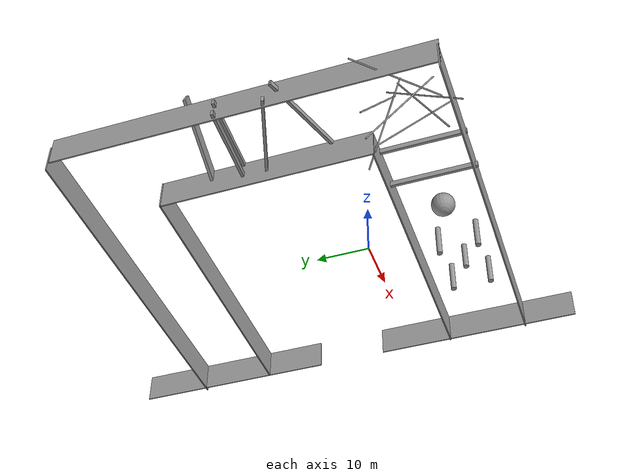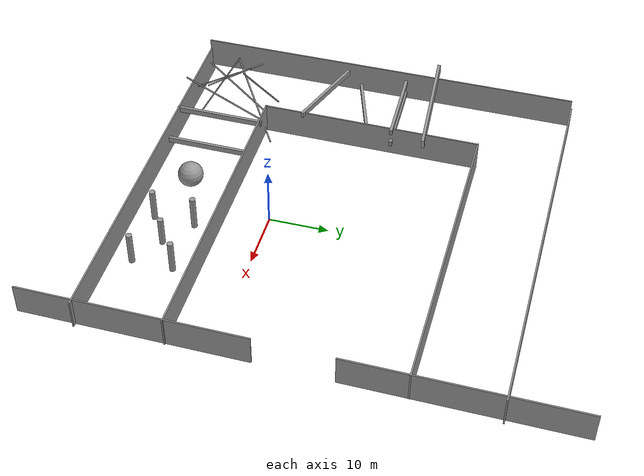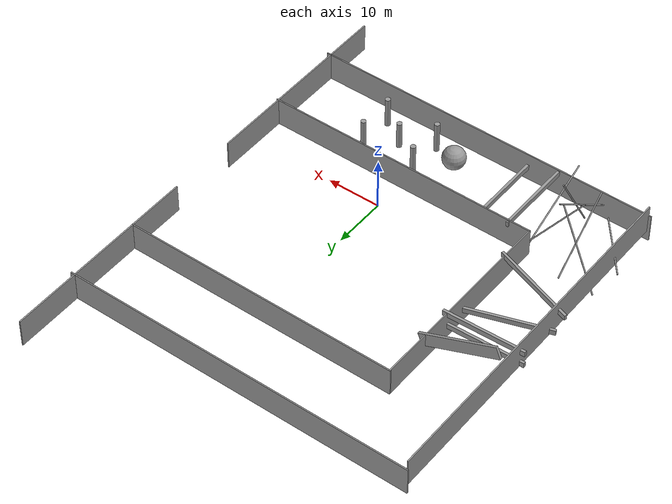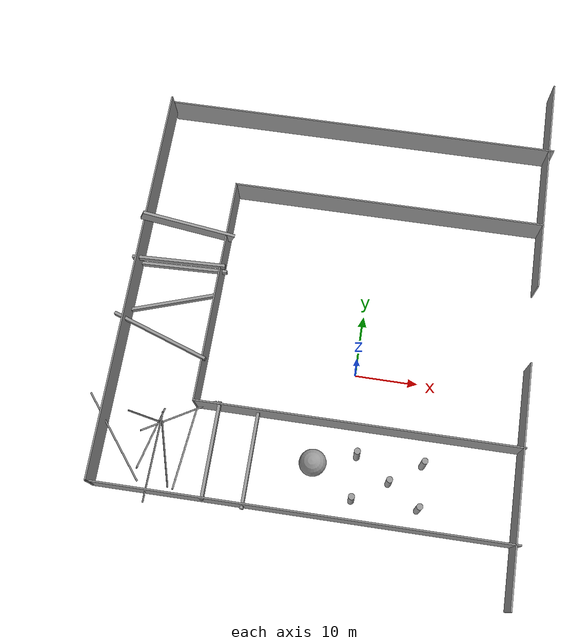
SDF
<?xml version='1.0'?>
<sdf version='1.6'>
  <model name='prueba_dron_0'>
    <link name='link'>
      <pose frame=''>-5.24977 -22.9832 0 0 -0 0</pose>
      <inertial>
        <mass>85.7654</mass>
        <inertia>
          <ixx>212.016</ixx>
          <ixy>0</ixy>
          <ixz>0</ixz>
          <iyy>32312.3</iyy>
          <iyz>0</iyz>
          <izz>32101.1</izz>
        </inertia>
        <pose frame=''>0 0 0 0 -0 0</pose>
      </inertial>
      <self_collide>0</self_collide>
      <kinematic>0</kinematic>
      <visual name='visual'>
        <geometry>
          <box>
            <size>67.018 0.235169 5.44144</size>
          </box>
        </geometry>
        <material>
          <script>
            <name>Gazebo/Grey</name>
            <uri>file://media/materials/scripts/gazebo.material</uri>
          </script>
          <ambient>0.3 0.3 0.3 1</ambient>
          <diffuse>0.7 0.7 0.7 1</diffuse>
          <specular>0.01 0.01 0.01 1</specular>
          <emissive>0 0 0 1</emissive>
        </material>
        <pose frame=''>0 0 0 0 -0 0</pose>
        <cast_shadows>1</cast_shadows>
        <transparency>0</transparency>
      </visual>
      <collision name='collision'>
        <laser_retro>0</laser_retro>
        <max_contacts>10</max_contacts>
        <pose frame=''>0 0 0 0 -0 0</pose>
        <geometry>
          <box>
            <size>67.018 0.235169 5.44144</size>
          </box>
        </geometry>
        <surface>
          <friction>
            <ode>
              <mu>1</mu>
              <mu2>1</mu2>
              <fdir1>0 0 0</fdir1>
              <slip1>0</slip1>
              <slip2>0</slip2>
            </ode>
            <torsional>
              <coefficient>1</coefficient>
              <patch_radius>0</patch_radius>
              <surface_radius>0</surface_radius>
              <use_patch_radius>1</use_patch_radius>
              <ode>
                <slip>0</slip>
              </ode>
            </torsional>
          </friction>
          <bounce>
            <restitution_coefficient>0</restitution_coefficient>
            <threshold>1e+06</threshold>
          </bounce>
          <contact>
            <collide_without_contact>0</collide_without_contact>
            <collide_without_contact_bitmask>1</collide_without_contact_bitmask>
            <collide_bitmask>1</collide_bitmask>
            <ode>
              <soft_cfm>0</soft_cfm>
              <soft_erp>0.2</soft_erp>
              <kp>1e+13</kp>
              <kd>1</kd>
              <max_vel>0.01</max_vel>
              <min_depth>0</min_depth>
            </ode>
            <bullet>
              <split_impulse>1</split_impulse>
              <split_impulse_penetration_threshold>-0.01</split_impulse_penetration_threshold>
              <soft_cfm>0</soft_cfm>
              <soft_erp>0.2</soft_erp>
              <kp>1e+13</kp>
              <kd>1</kd>
            </bullet>
          </contact>
        </surface>
      </collision>
    </link>
    <link name='link_0'>
      <pose frame=''>12.4694 -19.5562 -0 0 -0 0</pose>
      <inertial>
        <mass>5.87851</mass>
        <inertia>
          <ixx>17.2959</ixx>
          <ixy>0</ixy>
          <ixz>0</ixz>
          <iyy>17.2959</iyy>
          <iyz>0</iyz>
          <izz>0.734814</izz>
        </inertia>
        <pose frame=''>0 0 0 0 -0 0</pose>
      </inertial>
      <self_collide>0</self_collide>
      <kinematic>0</kinematic>
      <visual name='visual'>
        <pose frame=''>0 0 0 0 -0 0</pose>
        <geometry>
          <cylinder>
            <radius>0.5</radius>
            <length>5.87852</length>
          </cylinder>
        </geometry>
        <material>
          <lighting>1</lighting>
          <script>
            <uri>file://media/materials/scripts/gazebo.material</uri>
            <name>Gazebo/Grey</name>
          </script>
          <ambient>0.3 0.3 0.3 1</ambient>
          <diffuse>0.7 0.7 0.7 1</diffuse>
          <specular>0.01 0.01 0.01 1</specular>
          <emissive>0 0 0 1</emissive>
        </material>
        <cast_shadows>1</cast_shadows>
        <transparency>0</transparency>
      </visual>
      <collision name='collision'>
        <laser_retro>0</laser_retro>
        <max_contacts>10</max_contacts>
        <pose frame=''>0 0 0 0 -0 0</pose>
        <geometry>
          <cylinder>
            <radius>0.5</radius>
            <length>5.87852</length>
          </cylinder>
        </geometry>
        <surface>
          <friction>
            <ode>
              <mu>1</mu>
              <mu2>1</mu2>
              <fdir1>0 0 0</fdir1>
              <slip1>0</slip1>
              <slip2>0</slip2>
            </ode>
            <torsional>
              <coefficient>1</coefficient>
              <patch_radius>0</patch_radius>
              <surface_radius>0</surface_radius>
              <use_patch_radius>1</use_patch_radius>
              <ode>
                <slip>0</slip>
              </ode>
            </torsional>
          </friction>
          <bounce>
            <restitution_coefficient>0</restitution_coefficient>
            <threshold>1e+06</threshold>
          </bounce>
          <contact>
            <collide_without_contact>0</collide_without_contact>
            <collide_without_contact_bitmask>1</collide_without_contact_bitmask>
            <collide_bitmask>1</collide_bitmask>
            <ode>
              <soft_cfm>0</soft_cfm>
              <soft_erp>0.2</soft_erp>
              <kp>1e+13</kp>
              <kd>1</kd>
              <max_vel>0.01</max_vel>
              <min_depth>0</min_depth>
            </ode>
            <bullet>
              <split_impulse>1</split_impulse>
              <split_impulse_penetration_threshold>-0.01</split_impulse_penetration_threshold>
              <soft_cfm>0</soft_cfm>
              <soft_erp>0.2</soft_erp>
              <kp>1e+13</kp>
              <kd>1</kd>
            </bullet>
          </contact>
        </surface>
      </collision>
    </link>
    <link name='link_1'>
      <pose frame=''>12.4694 -12.5562 -0 0 -0 0</pose>
      <inertial>
        <mass>5.95576</mass>
        <inertia>
          <ixx>17.977</ixx>
          <ixy>0</ixy>
          <ixz>0</ixz>
          <iyy>17.977</iyy>
          <iyz>0</iyz>
          <izz>0.74447</izz>
        </inertia>
        <pose frame=''>0 0 0 0 -0 0</pose>
      </inertial>
      <self_collide>0</self_collide>
      <kinematic>0</kinematic>
      <visual name='visual'>
        <pose frame=''>0 0 0 0 -0 0</pose>
        <geometry>
          <cylinder>
            <radius>0.5</radius>
            <length>5.95576</length>
          </cylinder>
        </geometry>
        <material>
          <lighting>1</lighting>
          <script>
            <uri>file://media/materials/scripts/gazebo.material</uri>
            <name>Gazebo/Grey</name>
          </script>
          <ambient>0.3 0.3 0.3 1</ambient>
          <diffuse>0.7 0.7 0.7 1</diffuse>
          <specular>0.01 0.01 0.01 1</specular>
          <emissive>0 0 0 1</emissive>
        </material>
        <cast_shadows>1</cast_shadows>
        <transparency>0</transparency>
      </visual>
      <collision name='collision'>
        <laser_retro>0</laser_retro>
        <max_contacts>10</max_contacts>
        <pose frame=''>0 0 0 0 -0 0</pose>
        <geometry>
          <cylinder>
            <radius>0.5</radius>
            <length>5.95576</length>
          </cylinder>
        </geometry>
        <surface>
          <friction>
            <ode>
              <mu>1</mu>
              <mu2>1</mu2>
              <fdir1>0 0 0</fdir1>
              <slip1>0</slip1>
              <slip2>0</slip2>
            </ode>
            <torsional>
              <coefficient>1</coefficient>
              <patch_radius>0</patch_radius>
              <surface_radius>0</surface_radius>
              <use_patch_radius>1</use_patch_radius>
              <ode>
                <slip>0</slip>
              </ode>
            </torsional>
          </friction>
          <bounce>
            <restitution_coefficient>0</restitution_coefficient>
            <threshold>1e+06</threshold>
          </bounce>
          <contact>
            <collide_without_contact>0</collide_without_contact>
            <collide_without_contact_bitmask>1</collide_without_contact_bitmask>
            <collide_bitmask>1</collide_bitmask>
            <ode>
              <soft_cfm>0</soft_cfm>
              <soft_erp>0.2</soft_erp>
              <kp>1e+13</kp>
              <kd>1</kd>
              <max_vel>0.01</max_vel>
              <min_depth>0</min_depth>
            </ode>
            <bullet>
              <split_impulse>1</split_impulse>
              <split_impulse_penetration_threshold>-0.01</split_impulse_penetration_threshold>
              <soft_cfm>0</soft_cfm>
              <soft_erp>0.2</soft_erp>
              <kp>1e+13</kp>
              <kd>1</kd>
            </bullet>
          </contact>
        </surface>
      </collision>
    </link>
    <link name='link_2'>
      <pose frame=''>7.46938 -16.1137 -0 0 -0 0</pose>
      <inertial>
        <mass>5.24847</mass>
        <inertia>
          <ixx>12.3761</ixx>
          <ixy>0</ixy>
          <ixz>0</ixz>
          <iyy>12.3761</iyy>
          <iyz>0</iyz>
          <izz>0.656059</izz>
        </inertia>
        <pose frame=''>0 0 0 0 -0 0</pose>
      </inertial>
      <self_collide>0</self_collide>
      <kinematic>0</kinematic>
      <visual name='visual'>
        <pose frame=''>0 0 0 0 -0 0</pose>
        <geometry>
          <cylinder>
            <radius>0.5</radius>
            <length>5.24847</length>
          </cylinder>
        </geometry>
        <material>
          <lighting>1</lighting>
          <script>
            <uri>file://media/materials/scripts/gazebo.material</uri>
            <name>Gazebo/Grey</name>
          </script>
          <ambient>0.3 0.3 0.3 1</ambient>
          <diffuse>0.7 0.7 0.7 1</diffuse>
          <specular>0.01 0.01 0.01 1</specular>
          <emissive>0 0 0 1</emissive>
        </material>
        <cast_shadows>1</cast_shadows>
        <transparency>0</transparency>
      </visual>
      <collision name='collision'>
        <laser_retro>0</laser_retro>
        <max_contacts>10</max_contacts>
        <pose frame=''>0 0 0 0 -0 0</pose>
        <geometry>
          <cylinder>
            <radius>0.5</radius>
            <length>5.24847</length>
          </cylinder>
        </geometry>
        <surface>
          <friction>
            <ode>
              <mu>1</mu>
              <mu2>1</mu2>
              <fdir1>0 0 0</fdir1>
              <slip1>0</slip1>
              <slip2>0</slip2>
            </ode>
            <torsional>
              <coefficient>1</coefficient>
              <patch_radius>0</patch_radius>
              <surface_radius>0</surface_radius>
              <use_patch_radius>1</use_patch_radius>
              <ode>
                <slip>0</slip>
              </ode>
            </torsional>
          </friction>
          <bounce>
            <restitution_coefficient>0</restitution_coefficient>
            <threshold>1e+06</threshold>
          </bounce>
          <contact>
            <collide_without_contact>0</collide_without_contact>
            <collide_without_contact_bitmask>1</collide_without_contact_bitmask>
            <collide_bitmask>1</collide_bitmask>
            <ode>
              <soft_cfm>0</soft_cfm>
              <soft_erp>0.2</soft_erp>
              <kp>1e+13</kp>
              <kd>1</kd>
              <max_vel>0.01</max_vel>
              <min_depth>0</min_depth>
            </ode>
            <bullet>
              <split_impulse>1</split_impulse>
              <split_impulse_penetration_threshold>-0.01</split_impulse_penetration_threshold>
              <soft_cfm>0</soft_cfm>
              <soft_erp>0.2</soft_erp>
              <kp>1e+13</kp>
              <kd>1</kd>
            </bullet>
          </contact>
        </surface>
      </collision>
    </link>
    <link name='link_3'>
      <pose frame=''>1.98284 -12.5562 -0 0 -0 0</pose>
      <inertial>
        <mass>6.1347</mass>
        <inertia>
          <ixx>19.6231</ixx>
          <ixy>0</ixy>
          <ixz>0</ixz>
          <iyy>19.6231</iyy>
          <iyz>0</iyz>
          <izz>0.766838</izz>
        </inertia>
        <pose frame=''>0 0 0 0 -0 0</pose>
      </inertial>
      <self_collide>0</self_collide>
      <kinematic>0</kinematic>
      <visual name='visual'>
        <pose frame=''>0 0 0 0 -0 0</pose>
        <geometry>
          <cylinder>
            <radius>0.5</radius>
            <length>6.1347</length>
          </cylinder>
        </geometry>
        <material>
          <lighting>1</lighting>
          <script>
            <uri>file://media/materials/scripts/gazebo.material</uri>
            <name>Gazebo/Grey</name>
          </script>
          <ambient>0.3 0.3 0.3 1</ambient>
          <diffuse>0.7 0.7 0.7 1</diffuse>
          <specular>0.01 0.01 0.01 1</specular>
          <emissive>0 0 0 1</emissive>
        </material>
        <cast_shadows>1</cast_shadows>
        <transparency>0</transparency>
      </visual>
      <collision name='collision'>
        <laser_retro>0</laser_retro>
        <max_contacts>10</max_contacts>
        <pose frame=''>0 0 0 0 -0 0</pose>
        <geometry>
          <cylinder>
            <radius>0.5</radius>
            <length>6.1347</length>
          </cylinder>
        </geometry>
        <surface>
          <friction>
            <ode>
              <mu>1</mu>
              <mu2>1</mu2>
              <fdir1>0 0 0</fdir1>
              <slip1>0</slip1>
              <slip2>0</slip2>
            </ode>
            <torsional>
              <coefficient>1</coefficient>
              <patch_radius>0</patch_radius>
              <surface_radius>0</surface_radius>
              <use_patch_radius>1</use_patch_radius>
              <ode>
                <slip>0</slip>
              </ode>
            </torsional>
          </friction>
          <bounce>
            <restitution_coefficient>0</restitution_coefficient>
            <threshold>1e+06</threshold>
          </bounce>
          <contact>
            <collide_without_contact>0</collide_without_contact>
            <collide_without_contact_bitmask>1</collide_without_contact_bitmask>
            <collide_bitmask>1</collide_bitmask>
            <ode>
              <soft_cfm>0</soft_cfm>
              <soft_erp>0.2</soft_erp>
              <kp>1e+13</kp>
              <kd>1</kd>
              <max_vel>0.01</max_vel>
              <min_depth>0</min_depth>
            </ode>
            <bullet>
              <split_impulse>1</split_impulse>
              <split_impulse_penetration_threshold>-0.01</split_impulse_penetration_threshold>
              <soft_cfm>0</soft_cfm>
              <soft_erp>0.2</soft_erp>
              <kp>1e+13</kp>
              <kd>1</kd>
            </bullet>
          </contact>
        </surface>
      </collision>
    </link>
    <link name='link_4'>
      <pose frame=''>2.03774 -19.5562 -0 0 -0 0</pose>
      <inertial>
        <mass>5.97726</mass>
        <inertia>
          <ixx>18.1697</ixx>
          <ixy>0</ixy>
          <ixz>0</ixz>
          <iyy>18.1697</iyy>
          <iyz>0</iyz>
          <izz>0.747158</izz>
        </inertia>
        <pose frame=''>0 0 0 0 -0 0</pose>
      </inertial>
      <self_collide>0</self_collide>
      <kinematic>0</kinematic>
      <visual name='visual'>
        <pose frame=''>0 0 0 0 -0 0</pose>
        <geometry>
          <cylinder>
            <radius>0.5</radius>
            <length>5.97727</length>
          </cylinder>
        </geometry>
        <material>
          <lighting>1</lighting>
          <script>
            <uri>file://media/materials/scripts/gazebo.material</uri>
            <name>Gazebo/Grey</name>
          </script>
          <ambient>0.3 0.3 0.3 1</ambient>
          <diffuse>0.7 0.7 0.7 1</diffuse>
          <specular>0.01 0.01 0.01 1</specular>
          <emissive>0 0 0 1</emissive>
        </material>
        <cast_shadows>1</cast_shadows>
        <transparency>0</transparency>
      </visual>
      <collision name='collision'>
        <laser_retro>0</laser_retro>
        <max_contacts>10</max_contacts>
        <pose frame=''>0 0 0 0 -0 0</pose>
        <geometry>
          <cylinder>
            <radius>0.5</radius>
            <length>5.97727</length>
          </cylinder>
        </geometry>
        <surface>
          <friction>
            <ode>
              <mu>1</mu>
              <mu2>1</mu2>
              <fdir1>0 0 0</fdir1>
              <slip1>0</slip1>
              <slip2>0</slip2>
            </ode>
            <torsional>
              <coefficient>1</coefficient>
              <patch_radius>0</patch_radius>
              <surface_radius>0</surface_radius>
              <use_patch_radius>1</use_patch_radius>
              <ode>
                <slip>0</slip>
              </ode>
            </torsional>
          </friction>
          <bounce>
            <restitution_coefficient>0</restitution_coefficient>
            <threshold>1e+06</threshold>
          </bounce>
          <contact>
            <collide_without_contact>0</collide_without_contact>
            <collide_without_contact_bitmask>1</collide_without_contact_bitmask>
            <collide_bitmask>1</collide_bitmask>
            <ode>
              <soft_cfm>0</soft_cfm>
              <soft_erp>0.2</soft_erp>
              <kp>1e+13</kp>
              <kd>1</kd>
              <max_vel>0.01</max_vel>
              <min_depth>0</min_depth>
            </ode>
            <bullet>
              <split_impulse>1</split_impulse>
              <split_impulse_penetration_threshold>-0.01</split_impulse_penetration_threshold>
              <soft_cfm>0</soft_cfm>
              <soft_erp>0.2</soft_erp>
              <kp>1e+13</kp>
              <kd>1</kd>
            </bullet>
          </contact>
        </surface>
      </collision>
    </link>
    <link name='link_5'>
      <pose frame=''>-4.60337 -15.2115 2.23467 0 -0 0</pose>
      <inertial>
        <mass>78.0965</mass>
        <inertia>
          <ixx>142.687</ixx>
          <ixy>0</ixy>
          <ixz>0</ixz>
          <iyy>142.687</iyy>
          <iyz>0</iyz>
          <izz>142.687</izz>
        </inertia>
        <pose frame=''>0 0 0 0 -0 0</pose>
      </inertial>
      <self_collide>0</self_collide>
      <kinematic>0</kinematic>
      <visual name='visual'>
        <pose frame=''>0 0 0 0 -0 0</pose>
        <geometry>
          <sphere>
            <radius>2.13721</radius>
          </sphere>
        </geometry>
        <material>
          <lighting>1</lighting>
          <script>
            <uri>file://media/materials/scripts/gazebo.material</uri>
            <name>Gazebo/Grey</name>
          </script>
          <ambient>0.3 0.3 0.3 1</ambient>
          <diffuse>0.7 0.7 0.7 1</diffuse>
          <specular>0.01 0.01 0.01 1</specular>
          <emissive>0 0 0 1</emissive>
        </material>
        <cast_shadows>1</cast_shadows>
        <transparency>0</transparency>
      </visual>
      <collision name='collision'>
        <laser_retro>0</laser_retro>
        <max_contacts>10</max_contacts>
        <pose frame=''>0 0 0 0 -0 0</pose>
        <geometry>
          <sphere>
            <radius>2.13721</radius>
          </sphere>
        </geometry>
        <surface>
          <friction>
            <ode>
              <mu>1</mu>
              <mu2>1</mu2>
              <fdir1>0 0 0</fdir1>
              <slip1>0</slip1>
              <slip2>0</slip2>
            </ode>
            <torsional>
              <coefficient>1</coefficient>
              <patch_radius>0</patch_radius>
              <surface_radius>0</surface_radius>
              <use_patch_radius>1</use_patch_radius>
              <ode>
                <slip>0</slip>
              </ode>
            </torsional>
          </friction>
          <bounce>
            <restitution_coefficient>0</restitution_coefficient>
            <threshold>1e+06</threshold>
          </bounce>
          <contact>
            <collide_without_contact>0</collide_without_contact>
            <collide_without_contact_bitmask>1</collide_without_contact_bitmask>
            <collide_bitmask>1</collide_bitmask>
            <ode>
              <soft_cfm>0</soft_cfm>
              <soft_erp>0.2</soft_erp>
              <kp>1e+13</kp>
              <kd>1</kd>
              <max_vel>0.01</max_vel>
              <min_depth>0</min_depth>
            </ode>
            <bullet>
              <split_impulse>1</split_impulse>
              <split_impulse_penetration_threshold>-0.01</split_impulse_penetration_threshold>
              <soft_cfm>0</soft_cfm>
              <soft_erp>0.2</soft_erp>
              <kp>1e+13</kp>
              <kd>1</kd>
            </bullet>
          </contact>
        </surface>
      </collision>
    </link>
    <link name='link_6'>
      <pose frame=''>-14.4826 -15.8376 -0 0 -0 0</pose>
      <inertial>
        <mass>7.64164</mass>
        <inertia>
          <ixx>152.705</ixx>
          <ixy>0</ixy>
          <ixz>0</ixz>
          <iyy>0.792526</iyy>
          <iyz>0</iyz>
          <izz>152.224</izz>
        </inertia>
        <pose frame=''>0 0 0 0 -0 0</pose>
      </inertial>
      <self_collide>0</self_collide>
      <kinematic>0</kinematic>
      <visual name='visual'>
        <pose frame=''>0 0 0 0 -0 0</pose>
        <geometry>
          <box>
            <size>0.494495 15.4531 1</size>
          </box>
        </geometry>
        <material>
          <lighting>1</lighting>
          <script>
            <uri>file://media/materials/scripts/gazebo.material</uri>
            <name>Gazebo/Grey</name>
          </script>
          <ambient>0.3 0.3 0.3 1</ambient>
          <diffuse>0.7 0.7 0.7 1</diffuse>
          <specular>0.01 0.01 0.01 1</specular>
          <emissive>0 0 0 1</emissive>
        </material>
        <cast_shadows>1</cast_shadows>
        <transparency>0</transparency>
      </visual>
      <collision name='collision'>
        <laser_retro>0</laser_retro>
        <max_contacts>10</max_contacts>
        <pose frame=''>0 0 0 0 -0 0</pose>
        <geometry>
          <box>
            <size>0.494495 15.4531 1</size>
          </box>
        </geometry>
        <surface>
          <friction>
            <ode>
              <mu>1</mu>
              <mu2>1</mu2>
              <fdir1>0 0 0</fdir1>
              <slip1>0</slip1>
              <slip2>0</slip2>
            </ode>
            <torsional>
              <coefficient>1</coefficient>
              <patch_radius>0</patch_radius>
              <surface_radius>0</surface_radius>
              <use_patch_radius>1</use_patch_radius>
              <ode>
                <slip>0</slip>
              </ode>
            </torsional>
          </friction>
          <bounce>
            <restitution_coefficient>0</restitution_coefficient>
            <threshold>1e+06</threshold>
          </bounce>
          <contact>
            <collide_without_contact>0</collide_without_contact>
            <collide_without_contact_bitmask>1</collide_without_contact_bitmask>
            <collide_bitmask>1</collide_bitmask>
            <ode>
              <soft_cfm>0</soft_cfm>
              <soft_erp>0.2</soft_erp>
              <kp>1e+13</kp>
              <kd>1</kd>
              <max_vel>0.01</max_vel>
              <min_depth>0</min_depth>
            </ode>
            <bullet>
              <split_impulse>1</split_impulse>
              <split_impulse_penetration_threshold>-0.01</split_impulse_penetration_threshold>
              <soft_cfm>0</soft_cfm>
              <soft_erp>0.2</soft_erp>
              <kp>1e+13</kp>
              <kd>1</kd>
            </bullet>
          </contact>
        </surface>
      </collision>
    </link>
    <link name='link_6_clone'>
      <pose frame=''>-20.5306 -15.5562 2.00301 0 -0 0</pose>
      <inertial>
        <mass>7.64164</mass>
        <inertia>
          <ixx>152.705</ixx>
          <ixy>0</ixy>
          <ixz>0</ixz>
          <iyy>0.792526</iyy>
          <iyz>0</iyz>
          <izz>152.224</izz>
        </inertia>
        <pose frame=''>0 0 0 0 -0 0</pose>
      </inertial>
      <self_collide>0</self_collide>
      <kinematic>0</kinematic>
      <visual name='visual'>
        <pose frame=''>0 0 0 0 -0 0</pose>
        <geometry>
          <box>
            <size>0.494495 15.4531 1</size>
          </box>
        </geometry>
        <material>
          <lighting>1</lighting>
          <script>
            <uri>file://media/materials/scripts/gazebo.material</uri>
            <name>Gazebo/Grey</name>
          </script>
          <ambient>0.3 0.3 0.3 1</ambient>
          <diffuse>0.7 0.7 0.7 1</diffuse>
          <specular>0.01 0.01 0.01 1</specular>
          <emissive>0 0 0 1</emissive>
          <shader type='pixel'/>
        </material>
        <cast_shadows>1</cast_shadows>
        <transparency>0</transparency>
      </visual>
      <collision name='collision'>
        <laser_retro>0</laser_retro>
        <max_contacts>10</max_contacts>
        <pose frame=''>0 0 0 0 -0 0</pose>
        <geometry>
          <box>
            <size>0.494495 15.4531 1</size>
          </box>
        </geometry>
        <surface>
          <friction>
            <ode>
              <mu>1</mu>
              <mu2>1</mu2>
              <fdir1>0 0 0</fdir1>
              <slip1>0</slip1>
              <slip2>0</slip2>
            </ode>
            <torsional>
              <coefficient>1</coefficient>
              <patch_radius>0</patch_radius>
              <surface_radius>0</surface_radius>
              <use_patch_radius>1</use_patch_radius>
              <ode>
                <slip>0</slip>
              </ode>
            </torsional>
          </friction>
          <bounce>
            <restitution_coefficient>0</restitution_coefficient>
            <threshold>1e+06</threshold>
          </bounce>
          <contact>
            <collide_without_contact>0</collide_without_contact>
            <collide_without_contact_bitmask>1</collide_without_contact_bitmask>
            <collide_bitmask>1</collide_bitmask>
            <ode>
              <soft_cfm>0</soft_cfm>
              <soft_erp>0.2</soft_erp>
              <kp>1e+13</kp>
              <kd>1</kd>
              <max_vel>0.01</max_vel>
              <min_depth>0</min_depth>
            </ode>
            <bullet>
              <split_impulse>1</split_impulse>
              <split_impulse_penetration_threshold>-0.01</split_impulse_penetration_threshold>
              <soft_cfm>0</soft_cfm>
              <soft_erp>0.2</soft_erp>
              <kp>1e+13</kp>
              <kd>1</kd>
            </bullet>
          </contact>
        </surface>
      </collision>
    </link>
    <link name='link_6_clone_clone'>
      <pose frame=''>-32.0268 1.35833 2.56444 0 -0 1.23777</pose>
      <inertial>
        <mass>8.31401</mass>
        <inertia>
          <ixx>196.537</ixx>
          <ixy>0</ixy>
          <ixz>0</ixz>
          <iyy>0.862258</iyy>
          <iyz>0</iyz>
          <izz>196.013</izz>
        </inertia>
        <pose frame=''>0 0 0 0 -0 0</pose>
      </inertial>
      <self_collide>0</self_collide>
      <kinematic>0</kinematic>
      <visual name='visual'>
        <pose frame=''>0 0 0 0 -0 0</pose>
        <geometry>
          <box>
            <size>0.494495 16.8128 1</size>
          </box>
        </geometry>
        <material>
          <lighting>1</lighting>
          <script>
            <uri>file://media/materials/scripts/gazebo.material</uri>
            <name>Gazebo/Grey</name>
          </script>
          <ambient>0.3 0.3 0.3 1</ambient>
          <diffuse>0.7 0.7 0.7 1</diffuse>
          <specular>0.01 0.01 0.01 1</specular>
          <emissive>0 0 0 1</emissive>
          <shader type='pixel'/>
        </material>
        <cast_shadows>1</cast_shadows>
        <transparency>0</transparency>
      </visual>
      <collision name='collision'>
        <laser_retro>0</laser_retro>
        <max_contacts>10</max_contacts>
        <pose frame=''>0 0 0 0 -0 0</pose>
        <geometry>
          <box>
            <size>0.494495 16.8128 1</size>
          </box>
        </geometry>
        <surface>
          <friction>
            <ode>
              <mu>1</mu>
              <mu2>1</mu2>
              <fdir1>0 0 0</fdir1>
              <slip1>0</slip1>
              <slip2>0</slip2>
            </ode>
            <torsional>
              <coefficient>1</coefficient>
              <patch_radius>0</patch_radius>
              <surface_radius>0</surface_radius>
              <use_patch_radius>1</use_patch_radius>
              <ode>
                <slip>0</slip>
              </ode>
            </torsional>
          </friction>
          <bounce>
            <restitution_coefficient>0</restitution_coefficient>
            <threshold>1e+06</threshold>
          </bounce>
          <contact>
            <collide_without_contact>0</collide_without_contact>
            <collide_without_contact_bitmask>1</collide_without_contact_bitmask>
            <collide_bitmask>1</collide_bitmask>
            <ode>
              <soft_cfm>0</soft_cfm>
              <soft_erp>0.2</soft_erp>
              <kp>1e+13</kp>
              <kd>1</kd>
              <max_vel>0.01</max_vel>
              <min_depth>0</min_depth>
            </ode>
            <bullet>
              <split_impulse>1</split_impulse>
              <split_impulse_penetration_threshold>-0.01</split_impulse_penetration_threshold>
              <soft_cfm>0</soft_cfm>
              <soft_erp>0.2</soft_erp>
              <kp>1e+13</kp>
              <kd>1</kd>
            </bullet>
          </contact>
        </surface>
      </collision>
    </link>
    <link name='link_6_clone_clone_clone'>
      <pose frame=''>-31.987 7.95678 -0.088563 0 -0 1.89398</pose>
      <inertial>
        <mass>7.64164</mass>
        <inertia>
          <ixx>152.705</ixx>
          <ixy>0</ixy>
          <ixz>0</ixz>
          <iyy>0.792526</iyy>
          <iyz>0</iyz>
          <izz>152.224</izz>
        </inertia>
        <pose frame=''>0 0 0 0 -0 0</pose>
      </inertial>
      <self_collide>0</self_collide>
      <kinematic>0</kinematic>
      <visual name='visual'>
        <pose frame=''>0 0 0 0 -0 0</pose>
        <geometry>
          <box>
            <size>0.494495 15.4531 1</size>
          </box>
        </geometry>
        <material>
          <lighting>1</lighting>
          <script>
            <uri>file://media/materials/scripts/gazebo.material</uri>
            <name>Gazebo/Grey</name>
          </script>
          <ambient>0.3 0.3 0.3 1</ambient>
          <diffuse>0.7 0.7 0.7 1</diffuse>
          <specular>0.01 0.01 0.01 1</specular>
          <emissive>0 0 0 1</emissive>
          <shader type='pixel'/>
        </material>
        <cast_shadows>1</cast_shadows>
        <transparency>0</transparency>
      </visual>
      <collision name='collision'>
        <laser_retro>0</laser_retro>
        <max_contacts>10</max_contacts>
        <pose frame=''>0 0 0 0 -0 0</pose>
        <geometry>
          <box>
            <size>0.494495 15.4531 1</size>
          </box>
        </geometry>
        <surface>
          <friction>
            <ode>
              <mu>1</mu>
              <mu2>1</mu2>
              <fdir1>0 0 0</fdir1>
              <slip1>0</slip1>
              <slip2>0</slip2>
            </ode>
            <torsional>
              <coefficient>1</coefficient>
              <patch_radius>0</patch_radius>
              <surface_radius>0</surface_radius>
              <use_patch_radius>1</use_patch_radius>
              <ode>
                <slip>0</slip>
              </ode>
            </torsional>
          </friction>
          <bounce>
            <restitution_coefficient>0</restitution_coefficient>
            <threshold>1e+06</threshold>
          </bounce>
          <contact>
            <collide_without_contact>0</collide_without_contact>
            <collide_without_contact_bitmask>1</collide_without_contact_bitmask>
            <collide_bitmask>1</collide_bitmask>
            <ode>
              <soft_cfm>0</soft_cfm>
              <soft_erp>0.2</soft_erp>
              <kp>1e+13</kp>
              <kd>1</kd>
              <max_vel>0.01</max_vel>
              <min_depth>0</min_depth>
            </ode>
            <bullet>
              <split_impulse>1</split_impulse>
              <split_impulse_penetration_threshold>-0.01</split_impulse_penetration_threshold>
              <soft_cfm>0</soft_cfm>
              <soft_erp>0.2</soft_erp>
              <kp>1e+13</kp>
              <kd>1</kd>
            </bullet>
          </contact>
        </surface>
      </collision>
    </link>
    <link name='link_6_clone_clone_clone_clone'>
      <pose frame=''>-31.5306 14.4438 -0.088563 0 -0 1.60461</pose>
      <inertial>
        <mass>7.64164</mass>
        <inertia>
          <ixx>152.705</ixx>
          <ixy>0</ixy>
          <ixz>0</ixz>
          <iyy>0.792526</iyy>
          <iyz>0</iyz>
          <izz>152.224</izz>
        </inertia>
        <pose frame=''>0 0 0 0 -0 0</pose>
      </inertial>
      <self_collide>0</self_collide>
      <kinematic>0</kinematic>
      <visual name='visual'>
        <pose frame=''>0 0 0 0 -0 0</pose>
        <geometry>
          <box>
            <size>0.494495 15.4531 1</size>
          </box>
        </geometry>
        <material>
          <lighting>1</lighting>
          <script>
            <uri>file://media/materials/scripts/gazebo.material</uri>
            <name>Gazebo/Grey</name>
          </script>
          <ambient>0.3 0.3 0.3 1</ambient>
          <diffuse>0.7 0.7 0.7 1</diffuse>
          <specular>0.01 0.01 0.01 1</specular>
          <emissive>0 0 0 1</emissive>
          <shader type='pixel'/>
        </material>
        <cast_shadows>1</cast_shadows>
        <transparency>0</transparency>
      </visual>
      <collision name='collision'>
        <laser_retro>0</laser_retro>
        <max_contacts>10</max_contacts>
        <pose frame=''>0 0 0 0 -0 0</pose>
        <geometry>
          <box>
            <size>0.494495 15.4531 1</size>
          </box>
        </geometry>
        <surface>
          <friction>
            <ode>
              <mu>1</mu>
              <mu2>1</mu2>
              <fdir1>0 0 0</fdir1>
              <slip1>0</slip1>
              <slip2>0</slip2>
            </ode>
            <torsional>
              <coefficient>1</coefficient>
              <patch_radius>0</patch_radius>
              <surface_radius>0</surface_radius>
              <use_patch_radius>1</use_patch_radius>
              <ode>
                <slip>0</slip>
              </ode>
            </torsional>
          </friction>
          <bounce>
            <restitution_coefficient>0</restitution_coefficient>
            <threshold>1e+06</threshold>
          </bounce>
          <contact>
            <collide_without_contact>0</collide_without_contact>
            <collide_without_contact_bitmask>1</collide_without_contact_bitmask>
            <collide_bitmask>1</collide_bitmask>
            <ode>
              <soft_cfm>0</soft_cfm>
              <soft_erp>0.2</soft_erp>
              <kp>1e+13</kp>
              <kd>1</kd>
              <max_vel>0.01</max_vel>
              <min_depth>0</min_depth>
            </ode>
            <bullet>
              <split_impulse>1</split_impulse>
              <split_impulse_penetration_threshold>-0.01</split_impulse_penetration_threshold>
              <soft_cfm>0</soft_cfm>
              <soft_erp>0.2</soft_erp>
              <kp>1e+13</kp>
              <kd>1</kd>
            </bullet>
          </contact>
        </surface>
      </collision>
    </link>
    <link name='link_6_clone_clone_clone_clone_clone'>
      <pose frame=''>-31.5539 14.445 2.48955 0 -0 1.60461</pose>
      <inertial>
        <mass>7.64164</mass>
        <inertia>
          <ixx>152.705</ixx>
          <ixy>0</ixy>
          <ixz>0</ixz>
          <iyy>0.792526</iyy>
          <iyz>0</iyz>
          <izz>152.224</izz>
        </inertia>
        <pose frame=''>0 0 0 0 -0 0</pose>
      </inertial>
      <self_collide>0</self_collide>
      <kinematic>0</kinematic>
      <visual name='visual'>
        <pose frame=''>0 0 0 0 -0 0</pose>
        <geometry>
          <box>
            <size>0.494495 15.4531 1</size>
          </box>
        </geometry>
        <material>
          <lighting>1</lighting>
          <script>
            <uri>file://media/materials/scripts/gazebo.material</uri>
            <name>Gazebo/Grey</name>
          </script>
          <ambient>0.3 0.3 0.3 1</ambient>
          <diffuse>0.7 0.7 0.7 1</diffuse>
          <specular>0.01 0.01 0.01 1</specular>
          <emissive>0 0 0 1</emissive>
          <shader type='pixel'/>
        </material>
        <cast_shadows>1</cast_shadows>
        <transparency>0</transparency>
      </visual>
      <collision name='collision'>
        <laser_retro>0</laser_retro>
        <max_contacts>10</max_contacts>
        <pose frame=''>0 0 0 0 -0 0</pose>
        <geometry>
          <box>
            <size>0.494495 15.4531 1</size>
          </box>
        </geometry>
        <surface>
          <friction>
            <ode>
              <mu>1</mu>
              <mu2>1</mu2>
              <fdir1>0 0 0</fdir1>
              <slip1>0</slip1>
              <slip2>0</slip2>
            </ode>
            <torsional>
              <coefficient>1</coefficient>
              <patch_radius>0</patch_radius>
              <surface_radius>0</surface_radius>
              <use_patch_radius>1</use_patch_radius>
              <ode>
                <slip>0</slip>
              </ode>
            </torsional>
          </friction>
          <bounce>
            <restitution_coefficient>0</restitution_coefficient>
            <threshold>1e+06</threshold>
          </bounce>
          <contact>
            <collide_without_contact>0</collide_without_contact>
            <collide_without_contact_bitmask>1</collide_without_contact_bitmask>
            <collide_bitmask>1</collide_bitmask>
            <ode>
              <soft_cfm>0</soft_cfm>
              <soft_erp>0.2</soft_erp>
              <kp>1e+13</kp>
              <kd>1</kd>
              <max_vel>0.01</max_vel>
              <min_depth>0</min_depth>
            </ode>
            <bullet>
              <split_impulse>1</split_impulse>
              <split_impulse_penetration_threshold>-0.01</split_impulse_penetration_threshold>
              <soft_cfm>0</soft_cfm>
              <soft_erp>0.2</soft_erp>
              <kp>1e+13</kp>
              <kd>1</kd>
            </bullet>
          </contact>
        </surface>
      </collision>
    </link>
    <link name='link_6_clone_clone_clone_clone_clone_clone'>
      <pose frame=''>-30.8869 20.2129 4.11657 0.383286 -0 1.60461</pose>
      <inertial>
        <mass>18.5249</mass>
        <inertia>
          <ixx>377.716</ixx>
          <ixy>0</ixy>
          <ixz>0</ixz>
          <iyy>9.44924</iyy>
          <iyz>0</iyz>
          <izz>369.022</izz>
        </inertia>
        <pose frame=''>0 0 0 0 -0 0</pose>
      </inertial>
      <self_collide>0</self_collide>
      <kinematic>0</kinematic>
      <visual name='visual'>
        <pose frame=''>0 0 0 0 -0 0</pose>
        <geometry>
          <box>
            <size>0.494495 15.4531 2.42421</size>
          </box>
        </geometry>
        <material>
          <lighting>1</lighting>
          <script>
            <uri>file://media/materials/scripts/gazebo.material</uri>
            <name>Gazebo/Grey</name>
          </script>
          <ambient>0.3 0.3 0.3 1</ambient>
          <diffuse>0.7 0.7 0.7 1</diffuse>
          <specular>0.01 0.01 0.01 1</specular>
          <emissive>0 0 0 1</emissive>
          <shader type='pixel'/>
        </material>
        <cast_shadows>1</cast_shadows>
        <transparency>0</transparency>
      </visual>
      <collision name='collision'>
        <laser_retro>0</laser_retro>
        <max_contacts>10</max_contacts>
        <pose frame=''>0 0 0 0 -0 0</pose>
        <geometry>
          <box>
            <size>0.494495 15.4531 2.42421</size>
          </box>
        </geometry>
        <surface>
          <friction>
            <ode>
              <mu>1</mu>
              <mu2>1</mu2>
              <fdir1>0 0 0</fdir1>
              <slip1>0</slip1>
              <slip2>0</slip2>
            </ode>
            <torsional>
              <coefficient>1</coefficient>
              <patch_radius>0</patch_radius>
              <surface_radius>0</surface_radius>
              <use_patch_radius>1</use_patch_radius>
              <ode>
                <slip>0</slip>
              </ode>
            </torsional>
          </friction>
          <bounce>
            <restitution_coefficient>0</restitution_coefficient>
            <threshold>1e+06</threshold>
          </bounce>
          <contact>
            <collide_without_contact>0</collide_without_contact>
            <collide_without_contact_bitmask>1</collide_without_contact_bitmask>
            <collide_bitmask>1</collide_bitmask>
            <ode>
              <soft_cfm>0</soft_cfm>
              <soft_erp>0.2</soft_erp>
              <kp>1e+13</kp>
              <kd>1</kd>
              <max_vel>0.01</max_vel>
              <min_depth>0</min_depth>
            </ode>
            <bullet>
              <split_impulse>1</split_impulse>
              <split_impulse_penetration_threshold>-0.01</split_impulse_penetration_threshold>
              <soft_cfm>0</soft_cfm>
              <soft_erp>0.2</soft_erp>
              <kp>1e+13</kp>
              <kd>1</kd>
            </bullet>
          </contact>
        </surface>
      </collision>
    </link>
    <link name='link_7'>
      <pose frame=''>-27.1506 -17.5633 3.42663 -0.522312 0 0</pose>
      <inertial>
        <mass>0.951436</mass>
        <inertia>
          <ixx>19.8593</ixx>
          <ixy>0</ixy>
          <ixz>0</ixz>
          <iyy>19.8593</iyy>
          <iyz>0</iyz>
          <izz>0.0071503</izz>
        </inertia>
        <pose frame=''>0 0 0 0 -0 0</pose>
      </inertial>
      <self_collide>0</self_collide>
      <kinematic>0</kinematic>
      <visual name='visual'>
        <pose frame=''>0 0 0 0 -0 0</pose>
        <geometry>
          <cylinder>
            <radius>0.122586</radius>
            <length>15.8251</length>
          </cylinder>
        </geometry>
        <material>
          <lighting>1</lighting>
          <script>
            <uri>file://media/materials/scripts/gazebo.material</uri>
            <name>Gazebo/Grey</name>
          </script>
          <ambient>0.3 0.3 0.3 1</ambient>
          <diffuse>0.7 0.7 0.7 1</diffuse>
          <specular>0.01 0.01 0.01 1</specular>
          <emissive>0 0 0 1</emissive>
        </material>
        <cast_shadows>1</cast_shadows>
        <transparency>0</transparency>
      </visual>
      <collision name='collision'>
        <laser_retro>0</laser_retro>
        <max_contacts>10</max_contacts>
        <pose frame=''>0 0 0 0 -0 0</pose>
        <geometry>
          <cylinder>
            <radius>0.122586</radius>
            <length>15.8251</length>
          </cylinder>
        </geometry>
        <surface>
          <friction>
            <ode>
              <mu>1</mu>
              <mu2>1</mu2>
              <fdir1>0 0 0</fdir1>
              <slip1>0</slip1>
              <slip2>0</slip2>
            </ode>
            <torsional>
              <coefficient>1</coefficient>
              <patch_radius>0</patch_radius>
              <surface_radius>0</surface_radius>
              <use_patch_radius>1</use_patch_radius>
              <ode>
                <slip>0</slip>
              </ode>
            </torsional>
          </friction>
          <bounce>
            <restitution_coefficient>0</restitution_coefficient>
            <threshold>1e+06</threshold>
          </bounce>
          <contact>
            <collide_without_contact>0</collide_without_contact>
            <collide_without_contact_bitmask>1</collide_without_contact_bitmask>
            <collide_bitmask>1</collide_bitmask>
            <ode>
              <soft_cfm>0</soft_cfm>
              <soft_erp>0.2</soft_erp>
              <kp>1e+13</kp>
              <kd>1</kd>
              <max_vel>0.01</max_vel>
              <min_depth>0</min_depth>
            </ode>
            <bullet>
              <split_impulse>1</split_impulse>
              <split_impulse_penetration_threshold>-0.01</split_impulse_penetration_threshold>
              <soft_cfm>0</soft_cfm>
              <soft_erp>0.2</soft_erp>
              <kp>1e+13</kp>
              <kd>1</kd>
            </bullet>
          </contact>
        </surface>
      </collision>
    </link>
    <link name='link_7_clone'>
      <pose frame=''>-24.4361 -15.6879 2.66609 1.11642 -0 0</pose>
      <inertial>
        <mass>0.951436</mass>
        <inertia>
          <ixx>19.8593</ixx>
          <ixy>0</ixy>
          <ixz>0</ixz>
          <iyy>19.8593</iyy>
          <iyz>0</iyz>
          <izz>0.0071503</izz>
        </inertia>
        <pose frame=''>0 0 0 0 -0 0</pose>
      </inertial>
      <self_collide>0</self_collide>
      <kinematic>0</kinematic>
      <visual name='visual'>
        <pose frame=''>0 0 0 0 -0 0</pose>
        <geometry>
          <cylinder>
            <radius>0.122586</radius>
            <length>15.8251</length>
          </cylinder>
        </geometry>
        <material>
          <lighting>1</lighting>
          <script>
            <uri>file://media/materials/scripts/gazebo.material</uri>
            <name>Gazebo/Grey</name>
          </script>
          <ambient>0.3 0.3 0.3 1</ambient>
          <diffuse>0.7 0.7 0.7 1</diffuse>
          <specular>0.01 0.01 0.01 1</specular>
          <emissive>0 0 0 1</emissive>
          <shader type='pixel'/>
        </material>
        <cast_shadows>1</cast_shadows>
        <transparency>0</transparency>
      </visual>
      <collision name='collision'>
        <laser_retro>0</laser_retro>
        <max_contacts>10</max_contacts>
        <pose frame=''>0 0 0 0 -0 0</pose>
        <geometry>
          <cylinder>
            <radius>0.122586</radius>
            <length>15.8251</length>
          </cylinder>
        </geometry>
        <surface>
          <friction>
            <ode>
              <mu>1</mu>
              <mu2>1</mu2>
              <fdir1>0 0 0</fdir1>
              <slip1>0</slip1>
              <slip2>0</slip2>
            </ode>
            <torsional>
              <coefficient>1</coefficient>
              <patch_radius>0</patch_radius>
              <surface_radius>0</surface_radius>
              <use_patch_radius>1</use_patch_radius>
              <ode>
                <slip>0</slip>
              </ode>
            </torsional>
          </friction>
          <bounce>
            <restitution_coefficient>0</restitution_coefficient>
            <threshold>1e+06</threshold>
          </bounce>
          <contact>
            <collide_without_contact>0</collide_without_contact>
            <collide_without_contact_bitmask>1</collide_without_contact_bitmask>
            <collide_bitmask>1</collide_bitmask>
            <ode>
              <soft_cfm>0</soft_cfm>
              <soft_erp>0.2</soft_erp>
              <kp>1e+13</kp>
              <kd>1</kd>
              <max_vel>0.01</max_vel>
              <min_depth>0</min_depth>
            </ode>
            <bullet>
              <split_impulse>1</split_impulse>
              <split_impulse_penetration_threshold>-0.01</split_impulse_penetration_threshold>
              <soft_cfm>0</soft_cfm>
              <soft_erp>0.2</soft_erp>
              <kp>1e+13</kp>
              <kd>1</kd>
            </bullet>
          </contact>
        </surface>
      </collision>
    </link>
    <link name='link_7_clone_0'>
      <pose frame=''>-26.3536 -10.8289 1.93794 2.44091 -0.559361 1.76414</pose>
      <inertial>
        <mass>0.951436</mass>
        <inertia>
          <ixx>19.8593</ixx>
          <ixy>0</ixy>
          <ixz>0</ixz>
          <iyy>19.8593</iyy>
          <iyz>0</iyz>
          <izz>0.0071503</izz>
        </inertia>
        <pose frame=''>0 0 0 0 -0 0</pose>
      </inertial>
      <self_collide>0</self_collide>
      <kinematic>0</kinematic>
      <visual name='visual'>
        <pose frame=''>0 0 0 0 -0 0</pose>
        <geometry>
          <cylinder>
            <radius>0.122586</radius>
            <length>15.8251</length>
          </cylinder>
        </geometry>
        <material>
          <lighting>1</lighting>
          <script>
            <uri>file://media/materials/scripts/gazebo.material</uri>
            <name>Gazebo/Grey</name>
          </script>
          <ambient>0.3 0.3 0.3 1</ambient>
          <diffuse>0.7 0.7 0.7 1</diffuse>
          <specular>0.01 0.01 0.01 1</specular>
          <emissive>0 0 0 1</emissive>
          <shader type='pixel'/>
        </material>
        <cast_shadows>1</cast_shadows>
        <transparency>0</transparency>
      </visual>
      <collision name='collision'>
        <laser_retro>0</laser_retro>
        <max_contacts>10</max_contacts>
        <pose frame=''>0 0 0 0 -0 0</pose>
        <geometry>
          <cylinder>
            <radius>0.122586</radius>
            <length>15.8251</length>
          </cylinder>
        </geometry>
        <surface>
          <friction>
            <ode>
              <mu>1</mu>
              <mu2>1</mu2>
              <fdir1>0 0 0</fdir1>
              <slip1>0</slip1>
              <slip2>0</slip2>
            </ode>
            <torsional>
              <coefficient>1</coefficient>
              <patch_radius>0</patch_radius>
              <surface_radius>0</surface_radius>
              <use_patch_radius>1</use_patch_radius>
              <ode>
                <slip>0</slip>
              </ode>
            </torsional>
          </friction>
          <bounce>
            <restitution_coefficient>0</restitution_coefficient>
            <threshold>1e+06</threshold>
          </bounce>
          <contact>
            <collide_without_contact>0</collide_without_contact>
            <collide_without_contact_bitmask>1</collide_without_contact_bitmask>
            <collide_bitmask>1</collide_bitmask>
            <ode>
              <soft_cfm>0</soft_cfm>
              <soft_erp>0.2</soft_erp>
              <kp>1e+13</kp>
              <kd>1</kd>
              <max_vel>0.01</max_vel>
              <min_depth>0</min_depth>
            </ode>
            <bullet>
              <split_impulse>1</split_impulse>
              <split_impulse_penetration_threshold>-0.01</split_impulse_penetration_threshold>
              <soft_cfm>0</soft_cfm>
              <soft_erp>0.2</soft_erp>
              <kp>1e+13</kp>
              <kd>1</kd>
            </bullet>
          </contact>
        </surface>
      </collision>
    </link>
    <link name='link_7_clone_1'>
      <pose frame=''>-28.9418 -18.2259 3.34926 -0.959238 0.13543 -0.078519</pose>
      <inertial>
        <mass>0.951436</mass>
        <inertia>
          <ixx>19.8593</ixx>
          <ixy>0</ixy>
          <ixz>0</ixz>
          <iyy>19.8593</iyy>
          <iyz>0</iyz>
          <izz>0.0071503</izz>
        </inertia>
        <pose frame=''>0 0 0 0 -0 0</pose>
      </inertial>
      <self_collide>0</self_collide>
      <kinematic>0</kinematic>
      <visual name='visual'>
        <pose frame=''>0 0 0 0 -0 0</pose>
        <geometry>
          <cylinder>
            <radius>0.122586</radius>
            <length>15.8251</length>
          </cylinder>
        </geometry>
        <material>
          <lighting>1</lighting>
          <script>
            <uri>file://media/materials/scripts/gazebo.material</uri>
            <name>Gazebo/Grey</name>
          </script>
          <ambient>0.3 0.3 0.3 1</ambient>
          <diffuse>0.7 0.7 0.7 1</diffuse>
          <specular>0.01 0.01 0.01 1</specular>
          <emissive>0 0 0 1</emissive>
          <shader type='pixel'/>
        </material>
        <cast_shadows>1</cast_shadows>
        <transparency>0</transparency>
      </visual>
      <collision name='collision'>
        <laser_retro>0</laser_retro>
        <max_contacts>10</max_contacts>
        <pose frame=''>0 0 0 0 -0 0</pose>
        <geometry>
          <cylinder>
            <radius>0.122586</radius>
            <length>15.8251</length>
          </cylinder>
        </geometry>
        <surface>
          <friction>
            <ode>
              <mu>1</mu>
              <mu2>1</mu2>
              <fdir1>0 0 0</fdir1>
              <slip1>0</slip1>
              <slip2>0</slip2>
            </ode>
            <torsional>
              <coefficient>1</coefficient>
              <patch_radius>0</patch_radius>
              <surface_radius>0</surface_radius>
              <use_patch_radius>1</use_patch_radius>
              <ode>
                <slip>0</slip>
              </ode>
            </torsional>
          </friction>
          <bounce>
            <restitution_coefficient>0</restitution_coefficient>
            <threshold>1e+06</threshold>
          </bounce>
          <contact>
            <collide_without_contact>0</collide_without_contact>
            <collide_without_contact_bitmask>1</collide_without_contact_bitmask>
            <collide_bitmask>1</collide_bitmask>
            <ode>
              <soft_cfm>0</soft_cfm>
              <soft_erp>0.2</soft_erp>
              <kp>1e+13</kp>
              <kd>1</kd>
              <max_vel>0.01</max_vel>
              <min_depth>0</min_depth>
            </ode>
            <bullet>
              <split_impulse>1</split_impulse>
              <split_impulse_penetration_threshold>-0.01</split_impulse_penetration_threshold>
              <soft_cfm>0</soft_cfm>
              <soft_erp>0.2</soft_erp>
              <kp>1e+13</kp>
              <kd>1</kd>
            </bullet>
          </contact>
        </surface>
      </collision>
    </link>
    <link name='link_7_clone_2'>
      <pose frame=''>-36.2913 -15.4597 0.511136 -1.34267 -0.703766 0.510448</pose>
      <inertial>
        <mass>0.951436</mass>
        <inertia>
          <ixx>19.8593</ixx>
          <ixy>0</ixy>
          <ixz>0</ixz>
          <iyy>19.8593</iyy>
          <iyz>0</iyz>
          <izz>0.0071503</izz>
        </inertia>
        <pose frame=''>0 0 0 0 -0 0</pose>
      </inertial>
      <self_collide>0</self_collide>
      <kinematic>0</kinematic>
      <visual name='visual'>
        <pose frame=''>0 0 0 0 -0 0</pose>
        <geometry>
          <cylinder>
            <radius>0.122586</radius>
            <length>15.8251</length>
          </cylinder>
        </geometry>
        <material>
          <lighting>1</lighting>
          <script>
            <uri>file://media/materials/scripts/gazebo.material</uri>
            <name>Gazebo/Grey</name>
          </script>
          <ambient>0.3 0.3 0.3 1</ambient>
          <diffuse>0.7 0.7 0.7 1</diffuse>
          <specular>0.01 0.01 0.01 1</specular>
          <emissive>0 0 0 1</emissive>
          <shader type='pixel'/>
        </material>
        <cast_shadows>1</cast_shadows>
        <transparency>0</transparency>
      </visual>
      <collision name='collision'>
        <laser_retro>0</laser_retro>
        <max_contacts>10</max_contacts>
        <pose frame=''>0 0 0 0 -0 0</pose>
        <geometry>
          <cylinder>
            <radius>0.122586</radius>
            <length>15.8251</length>
          </cylinder>
        </geometry>
        <surface>
          <friction>
            <ode>
              <mu>1</mu>
              <mu2>1</mu2>
              <fdir1>0 0 0</fdir1>
              <slip1>0</slip1>
              <slip2>0</slip2>
            </ode>
            <torsional>
              <coefficient>1</coefficient>
              <patch_radius>0</patch_radius>
              <surface_radius>0</surface_radius>
              <use_patch_radius>1</use_patch_radius>
              <ode>
                <slip>0</slip>
              </ode>
            </torsional>
          </friction>
          <bounce>
            <restitution_coefficient>0</restitution_coefficient>
            <threshold>1e+06</threshold>
          </bounce>
          <contact>
            <collide_without_contact>0</collide_without_contact>
            <collide_without_contact_bitmask>1</collide_without_contact_bitmask>
            <collide_bitmask>1</collide_bitmask>
            <ode>
              <soft_cfm>0</soft_cfm>
              <soft_erp>0.2</soft_erp>
              <kp>1e+13</kp>
              <kd>1</kd>
              <max_vel>0.01</max_vel>
              <min_depth>0</min_depth>
            </ode>
            <bullet>
              <split_impulse>1</split_impulse>
              <split_impulse_penetration_threshold>-0.01</split_impulse_penetration_threshold>
              <soft_cfm>0</soft_cfm>
              <soft_erp>0.2</soft_erp>
              <kp>1e+13</kp>
              <kd>1</kd>
            </bullet>
          </contact>
        </surface>
      </collision>
    </link>
    <link name='link_7_clone_3'>
      <pose frame=''>-30.526 -14.5562 0.113693 0.828801 -0 0</pose>
      <inertial>
        <mass>0.951436</mass>
        <inertia>
          <ixx>19.8593</ixx>
          <ixy>0</ixy>
          <ixz>0</ixz>
          <iyy>19.8593</iyy>
          <iyz>0</iyz>
          <izz>0.0071503</izz>
        </inertia>
        <pose frame=''>0 0 0 0 -0 0</pose>
      </inertial>
      <self_collide>0</self_collide>
      <kinematic>0</kinematic>
      <visual name='visual'>
        <pose frame=''>0 0 0 0 -0 0</pose>
        <geometry>
          <cylinder>
            <radius>0.122586</radius>
            <length>15.8251</length>
          </cylinder>
        </geometry>
        <material>
          <lighting>1</lighting>
          <script>
            <uri>file://media/materials/scripts/gazebo.material</uri>
            <name>Gazebo/Grey</name>
          </script>
          <ambient>0.3 0.3 0.3 1</ambient>
          <diffuse>0.7 0.7 0.7 1</diffuse>
          <specular>0.01 0.01 0.01 1</specular>
          <emissive>0 0 0 1</emissive>
          <shader type='pixel'/>
        </material>
        <cast_shadows>1</cast_shadows>
        <transparency>0</transparency>
      </visual>
      <collision name='collision'>
        <laser_retro>0</laser_retro>
        <max_contacts>10</max_contacts>
        <pose frame=''>0 0 0 0 -0 0</pose>
        <geometry>
          <cylinder>
            <radius>0.122586</radius>
            <length>15.8251</length>
          </cylinder>
        </geometry>
        <surface>
          <friction>
            <ode>
              <mu>1</mu>
              <mu2>1</mu2>
              <fdir1>0 0 0</fdir1>
              <slip1>0</slip1>
              <slip2>0</slip2>
            </ode>
            <torsional>
              <coefficient>1</coefficient>
              <patch_radius>0</patch_radius>
              <surface_radius>0</surface_radius>
              <use_patch_radius>1</use_patch_radius>
              <ode>
                <slip>0</slip>
              </ode>
            </torsional>
          </friction>
          <bounce>
            <restitution_coefficient>0</restitution_coefficient>
            <threshold>1e+06</threshold>
          </bounce>
          <contact>
            <collide_without_contact>0</collide_without_contact>
            <collide_without_contact_bitmask>1</collide_without_contact_bitmask>
            <collide_bitmask>1</collide_bitmask>
            <ode>
              <soft_cfm>0</soft_cfm>
              <soft_erp>0.2</soft_erp>
              <kp>1e+13</kp>
              <kd>1</kd>
              <max_vel>0.01</max_vel>
              <min_depth>0</min_depth>
            </ode>
            <bullet>
              <split_impulse>1</split_impulse>
              <split_impulse_penetration_threshold>-0.01</split_impulse_penetration_threshold>
              <soft_cfm>0</soft_cfm>
              <soft_erp>0.2</soft_erp>
              <kp>1e+13</kp>
              <kd>1</kd>
            </bullet>
          </contact>
        </surface>
      </collision>
    </link>
    <link name='link_7_clone_4'>
      <pose frame=''>-32.2181 -11.4726 0.168118 2.49269 -0.031623 -1.98694</pose>
      <inertial>
        <mass>0.951436</mass>
        <inertia>
          <ixx>19.8593</ixx>
          <ixy>0</ixy>
          <ixz>0</ixz>
          <iyy>19.8593</iyy>
          <iyz>0</iyz>
          <izz>0.0071503</izz>
        </inertia>
        <pose frame=''>0 0 0 0 -0 0</pose>
      </inertial>
      <self_collide>0</self_collide>
      <kinematic>0</kinematic>
      <visual name='visual'>
        <pose frame=''>0 0 0 0 -0 0</pose>
        <geometry>
          <cylinder>
            <radius>0.122586</radius>
            <length>15.8251</length>
          </cylinder>
        </geometry>
        <material>
          <lighting>1</lighting>
          <script>
            <uri>file://media/materials/scripts/gazebo.material</uri>
            <name>Gazebo/Grey</name>
          </script>
          <ambient>0.3 0.3 0.3 1</ambient>
          <diffuse>0.7 0.7 0.7 1</diffuse>
          <specular>0.01 0.01 0.01 1</specular>
          <emissive>0 0 0 1</emissive>
          <shader type='pixel'/>
        </material>
        <cast_shadows>1</cast_shadows>
        <transparency>0</transparency>
      </visual>
      <collision name='collision'>
        <laser_retro>0</laser_retro>
        <max_contacts>10</max_contacts>
        <pose frame=''>0 0 0 0 -0 0</pose>
        <geometry>
          <cylinder>
            <radius>0.122586</radius>
            <length>15.8251</length>
          </cylinder>
        </geometry>
        <surface>
          <friction>
            <ode>
              <mu>1</mu>
              <mu2>1</mu2>
              <fdir1>0 0 0</fdir1>
              <slip1>0</slip1>
              <slip2>0</slip2>
            </ode>
            <torsional>
              <coefficient>1</coefficient>
              <patch_radius>0</patch_radius>
              <surface_radius>0</surface_radius>
              <use_patch_radius>1</use_patch_radius>
              <ode>
                <slip>0</slip>
              </ode>
            </torsional>
          </friction>
          <bounce>
            <restitution_coefficient>0</restitution_coefficient>
            <threshold>1e+06</threshold>
          </bounce>
          <contact>
            <collide_without_contact>0</collide_without_contact>
            <collide_without_contact_bitmask>1</collide_without_contact_bitmask>
            <collide_bitmask>1</collide_bitmask>
            <ode>
              <soft_cfm>0</soft_cfm>
              <soft_erp>0.2</soft_erp>
              <kp>1e+13</kp>
              <kd>1</kd>
              <max_vel>0.01</max_vel>
              <min_depth>0</min_depth>
            </ode>
            <bullet>
              <split_impulse>1</split_impulse>
              <split_impulse_penetration_threshold>-0.01</split_impulse_penetration_threshold>
              <soft_cfm>0</soft_cfm>
              <soft_erp>0.2</soft_erp>
              <kp>1e+13</kp>
              <kd>1</kd>
            </bullet>
          </contact>
        </surface>
      </collision>
    </link>
    <link name='link_clone'>
      <pose frame=''>-38.2499 10.4038 1.81381 0 -0 -1.5668</pose>
      <inertial>
        <mass>85.7654</mass>
        <inertia>
          <ixx>212.016</ixx>
          <ixy>0</ixy>
          <ixz>0</ixz>
          <iyy>32312.3</iyy>
          <iyz>0</iyz>
          <izz>32101.1</izz>
        </inertia>
        <pose frame=''>0 0 0 0 -0 0</pose>
      </inertial>
      <self_collide>0</self_collide>
      <kinematic>0</kinematic>
      <visual name='visual'>
        <geometry>
          <box>
            <size>67.018 0.235169 5.44144</size>
          </box>
        </geometry>
        <material>
          <script>
            <name>Gazebo/Grey</name>
            <uri>file://media/materials/scripts/gazebo.material</uri>
          </script>
          <ambient>0.3 0.3 0.3 1</ambient>
          <diffuse>0.7 0.7 0.7 1</diffuse>
          <specular>0.01 0.01 0.01 1</specular>
          <emissive>0 0 0 1</emissive>
          <shader type='pixel'/>
        </material>
        <pose frame=''>0 0 0 0 -0 0</pose>
        <cast_shadows>1</cast_shadows>
        <transparency>0</transparency>
      </visual>
      <collision name='collision'>
        <laser_retro>0</laser_retro>
        <max_contacts>10</max_contacts>
        <pose frame=''>0 0 0 0 -0 0</pose>
        <geometry>
          <box>
            <size>67.018 0.235169 5.44144</size>
          </box>
        </geometry>
        <surface>
          <friction>
            <ode>
              <mu>1</mu>
              <mu2>1</mu2>
              <fdir1>0 0 0</fdir1>
              <slip1>0</slip1>
              <slip2>0</slip2>
            </ode>
            <torsional>
              <coefficient>1</coefficient>
              <patch_radius>0</patch_radius>
              <surface_radius>0</surface_radius>
              <use_patch_radius>1</use_patch_radius>
              <ode>
                <slip>0</slip>
              </ode>
            </torsional>
          </friction>
          <bounce>
            <restitution_coefficient>0</restitution_coefficient>
            <threshold>1e+06</threshold>
          </bounce>
          <contact>
            <collide_without_contact>0</collide_without_contact>
            <collide_without_contact_bitmask>1</collide_without_contact_bitmask>
            <collide_bitmask>1</collide_bitmask>
            <ode>
              <soft_cfm>0</soft_cfm>
              <soft_erp>0.2</soft_erp>
              <kp>1e+13</kp>
              <kd>1</kd>
              <max_vel>0.01</max_vel>
              <min_depth>0</min_depth>
            </ode>
            <bullet>
              <split_impulse>1</split_impulse>
              <split_impulse_penetration_threshold>-0.01</split_impulse_penetration_threshold>
              <soft_cfm>0</soft_cfm>
              <soft_erp>0.2</soft_erp>
              <kp>1e+13</kp>
              <kd>1</kd>
            </bullet>
          </contact>
        </surface>
      </collision>
    </link>
    <link name='link_clone_0'>
      <pose frame=''>-5.09065 44.0154 1e-06 0 -0 0</pose>
      <inertial>
        <mass>85.7654</mass>
        <inertia>
          <ixx>212.016</ixx>
          <ixy>0</ixy>
          <ixz>0</ixz>
          <iyy>32312.3</iyy>
          <iyz>0</iyz>
          <izz>32101.1</izz>
        </inertia>
        <pose frame=''>0 0 0 0 -0 0</pose>
      </inertial>
      <self_collide>0</self_collide>
      <kinematic>0</kinematic>
      <visual name='visual'>
        <geometry>
          <box>
            <size>67.018 0.235169 5.44144</size>
          </box>
        </geometry>
        <material>
          <script>
            <name>Gazebo/Grey</name>
            <uri>file://media/materials/scripts/gazebo.material</uri>
          </script>
          <ambient>0.3 0.3 0.3 1</ambient>
          <diffuse>0.7 0.7 0.7 1</diffuse>
          <specular>0.01 0.01 0.01 1</specular>
          <emissive>0 0 0 1</emissive>
          <shader type='pixel'/>
        </material>
        <pose frame=''>0 0 0 0 -0 0</pose>
        <cast_shadows>1</cast_shadows>
        <transparency>0</transparency>
      </visual>
      <collision name='collision'>
        <laser_retro>0</laser_retro>
        <max_contacts>10</max_contacts>
        <pose frame=''>0 0 0 0 -0 0</pose>
        <geometry>
          <box>
            <size>67.018 0.235169 5.44144</size>
          </box>
        </geometry>
        <surface>
          <friction>
            <ode>
              <mu>1</mu>
              <mu2>1</mu2>
              <fdir1>0 0 0</fdir1>
              <slip1>0</slip1>
              <slip2>0</slip2>
            </ode>
            <torsional>
              <coefficient>1</coefficient>
              <patch_radius>0</patch_radius>
              <surface_radius>0</surface_radius>
              <use_patch_radius>1</use_patch_radius>
              <ode>
                <slip>0</slip>
              </ode>
            </torsional>
          </friction>
          <bounce>
            <restitution_coefficient>0</restitution_coefficient>
            <threshold>1e+06</threshold>
          </bounce>
          <contact>
            <collide_without_contact>0</collide_without_contact>
            <collide_without_contact_bitmask>1</collide_without_contact_bitmask>
            <collide_bitmask>1</collide_bitmask>
            <ode>
              <soft_cfm>0</soft_cfm>
              <soft_erp>0.2</soft_erp>
              <kp>1e+13</kp>
              <kd>1</kd>
              <max_vel>0.01</max_vel>
              <min_depth>0</min_depth>
            </ode>
            <bullet>
              <split_impulse>1</split_impulse>
              <split_impulse_penetration_threshold>-0.01</split_impulse_penetration_threshold>
              <soft_cfm>0</soft_cfm>
              <soft_erp>0.2</soft_erp>
              <kp>1e+13</kp>
              <kd>1</kd>
            </bullet>
          </contact>
        </surface>
      </collision>
    </link>
    <link name='link_clone_1'>
      <pose frame=''>1.45578 29.8545 0 0 -0 0</pose>
      <inertial>
        <mass>67.2785</mass>
        <inertia>
          <ixx>166.316</ixx>
          <ixy>0</ixy>
          <ixz>0</ixz>
          <iyy>15661.6</iyy>
          <iyz>0</iyz>
          <izz>15495.9</izz>
        </inertia>
        <pose frame=''>0 0 0 0 -0 0</pose>
      </inertial>
      <self_collide>0</self_collide>
      <kinematic>0</kinematic>
      <visual name='visual'>
        <geometry>
          <box>
            <size>52.5721 0.235169 5.44144</size>
          </box>
        </geometry>
        <material>
          <script>
            <name>Gazebo/Grey</name>
            <uri>file://media/materials/scripts/gazebo.material</uri>
          </script>
          <ambient>0.3 0.3 0.3 1</ambient>
          <diffuse>0.7 0.7 0.7 1</diffuse>
          <specular>0.01 0.01 0.01 1</specular>
          <emissive>0 0 0 1</emissive>
          <shader type='pixel'/>
        </material>
        <pose frame=''>0 0 0 0 -0 0</pose>
        <cast_shadows>1</cast_shadows>
        <transparency>0</transparency>
      </visual>
      <collision name='collision'>
        <laser_retro>0</laser_retro>
        <max_contacts>10</max_contacts>
        <pose frame=''>0 0 0 0 -0 0</pose>
        <geometry>
          <box>
            <size>52.5721 0.235169 5.44144</size>
          </box>
        </geometry>
        <surface>
          <friction>
            <ode>
              <mu>1</mu>
              <mu2>1</mu2>
              <fdir1>0 0 0</fdir1>
              <slip1>0</slip1>
              <slip2>0</slip2>
            </ode>
            <torsional>
              <coefficient>1</coefficient>
              <patch_radius>0</patch_radius>
              <surface_radius>0</surface_radius>
              <use_patch_radius>1</use_patch_radius>
              <ode>
                <slip>0</slip>
              </ode>
            </torsional>
          </friction>
          <bounce>
            <restitution_coefficient>0</restitution_coefficient>
            <threshold>1e+06</threshold>
          </bounce>
          <contact>
            <collide_without_contact>0</collide_without_contact>
            <collide_without_contact_bitmask>1</collide_without_contact_bitmask>
            <collide_bitmask>1</collide_bitmask>
            <ode>
              <soft_cfm>0</soft_cfm>
              <soft_erp>0.2</soft_erp>
              <kp>1e+13</kp>
              <kd>1</kd>
              <max_vel>0.01</max_vel>
              <min_depth>0</min_depth>
            </ode>
            <bullet>
              <split_impulse>1</split_impulse>
              <split_impulse_penetration_threshold>-0.01</split_impulse_penetration_threshold>
              <soft_cfm>0</soft_cfm>
              <soft_erp>0.2</soft_erp>
              <kp>1e+13</kp>
              <kd>1</kd>
            </bullet>
          </contact>
        </surface>
      </collision>
    </link>
    <link name='link_clone_1_clone'>
      <pose frame=''>1.55686 -8.21174 0 0 -0 0</pose>
      <inertial>
        <mass>67.2785</mass>
        <inertia>
          <ixx>166.316</ixx>
          <ixy>0</ixy>
          <ixz>0</ixz>
          <iyy>15661.6</iyy>
          <iyz>0</iyz>
          <izz>15495.9</izz>
        </inertia>
        <pose frame=''>0 0 0 0 -0 0</pose>
      </inertial>
      <self_collide>0</self_collide>
      <kinematic>0</kinematic>
      <visual name='visual'>
        <geometry>
          <box>
            <size>52.5721 0.235169 5.44144</size>
          </box>
        </geometry>
        <material>
          <script>
            <name>Gazebo/Grey</name>
            <uri>file://media/materials/scripts/gazebo.material</uri>
          </script>
          <ambient>0.3 0.3 0.3 1</ambient>
          <diffuse>0.7 0.7 0.7 1</diffuse>
          <specular>0.01 0.01 0.01 1</specular>
          <emissive>0 0 0 1</emissive>
          <shader type='pixel'/>
        </material>
        <pose frame=''>0 0 0 0 -0 0</pose>
        <cast_shadows>1</cast_shadows>
        <transparency>0</transparency>
      </visual>
      <collision name='collision'>
        <laser_retro>0</laser_retro>
        <max_contacts>10</max_contacts>
        <pose frame=''>0 0 0 0 -0 0</pose>
        <geometry>
          <box>
            <size>52.5721 0.235169 5.44144</size>
          </box>
        </geometry>
        <surface>
          <friction>
            <ode>
              <mu>1</mu>
              <mu2>1</mu2>
              <fdir1>0 0 0</fdir1>
              <slip1>0</slip1>
              <slip2>0</slip2>
            </ode>
            <torsional>
              <coefficient>1</coefficient>
              <patch_radius>0</patch_radius>
              <surface_radius>0</surface_radius>
              <use_patch_radius>1</use_patch_radius>
              <ode>
                <slip>0</slip>
              </ode>
            </torsional>
          </friction>
          <bounce>
            <restitution_coefficient>0</restitution_coefficient>
            <threshold>1e+06</threshold>
          </bounce>
          <contact>
            <collide_without_contact>0</collide_without_contact>
            <collide_without_contact_bitmask>1</collide_without_contact_bitmask>
            <collide_bitmask>1</collide_bitmask>
            <ode>
              <soft_cfm>0</soft_cfm>
              <soft_erp>0.2</soft_erp>
              <kp>1e+13</kp>
              <kd>1</kd>
              <max_vel>0.01</max_vel>
              <min_depth>0</min_depth>
            </ode>
            <bullet>
              <split_impulse>1</split_impulse>
              <split_impulse_penetration_threshold>-0.01</split_impulse_penetration_threshold>
              <soft_cfm>0</soft_cfm>
              <soft_erp>0.2</soft_erp>
              <kp>1e+13</kp>
              <kd>1</kd>
            </bullet>
          </contact>
        </surface>
      </collision>
    </link>
    <link name='link_clone_1_clone_0'>
      <pose frame=''>-24.6724 10.7869 -0 0 -0 1.57039</pose>
      <inertial>
        <mass>49.0208</mass>
        <inertia>
          <ixx>121.182</ixx>
          <ixy>0</ixy>
          <ixz>0</ixz>
          <iyy>6115</iyy>
          <iyz>0</iyz>
          <izz>5994.27</izz>
        </inertia>
        <pose frame=''>0 0 0 0 -0 0</pose>
      </inertial>
      <self_collide>0</self_collide>
      <kinematic>0</kinematic>
      <visual name='visual'>
        <geometry>
          <box>
            <size>38.3053 0.235169 5.44144</size>
          </box>
        </geometry>
        <material>
          <script>
            <name>Gazebo/Grey</name>
            <uri>file://media/materials/scripts/gazebo.material</uri>
          </script>
          <ambient>0.3 0.3 0.3 1</ambient>
          <diffuse>0.7 0.7 0.7 1</diffuse>
          <specular>0.01 0.01 0.01 1</specular>
          <emissive>0 0 0 1</emissive>
          <shader type='pixel'/>
        </material>
        <pose frame=''>0 0 0 0 -0 0</pose>
        <cast_shadows>1</cast_shadows>
        <transparency>0</transparency>
      </visual>
      <collision name='collision'>
        <laser_retro>0</laser_retro>
        <max_contacts>10</max_contacts>
        <pose frame=''>0 0 0 0 -0 0</pose>
        <geometry>
          <box>
            <size>38.3053 0.235169 5.44144</size>
          </box>
        </geometry>
        <surface>
          <friction>
            <ode>
              <mu>1</mu>
              <mu2>1</mu2>
              <fdir1>0 0 0</fdir1>
              <slip1>0</slip1>
              <slip2>0</slip2>
            </ode>
            <torsional>
              <coefficient>1</coefficient>
              <patch_radius>0</patch_radius>
              <surface_radius>0</surface_radius>
              <use_patch_radius>1</use_patch_radius>
              <ode>
                <slip>0</slip>
              </ode>
            </torsional>
          </friction>
          <bounce>
            <restitution_coefficient>0</restitution_coefficient>
            <threshold>1e+06</threshold>
          </bounce>
          <contact>
            <collide_without_contact>0</collide_without_contact>
            <collide_without_contact_bitmask>1</collide_without_contact_bitmask>
            <collide_bitmask>1</collide_bitmask>
            <ode>
              <soft_cfm>0</soft_cfm>
              <soft_erp>0.2</soft_erp>
              <kp>1e+13</kp>
              <kd>1</kd>
              <max_vel>0.01</max_vel>
              <min_depth>0</min_depth>
            </ode>
            <bullet>
              <split_impulse>1</split_impulse>
              <split_impulse_penetration_threshold>-0.01</split_impulse_penetration_threshold>
              <soft_cfm>0</soft_cfm>
              <soft_erp>0.2</soft_erp>
              <kp>1e+13</kp>
              <kd>1</kd>
            </bullet>
          </contact>
        </surface>
      </collision>
    </link>
    <link name='link_clone_1_clone_0_clone'>
      <pose frame=''>27.4694 -13.5562 -0 0 -0 1.57039</pose>
      <inertial>
        <mass>49.0208</mass>
        <inertia>
          <ixx>121.182</ixx>
          <ixy>0</ixy>
          <ixz>0</ixz>
          <iyy>6115</iyy>
          <iyz>0</iyz>
          <izz>5994.27</izz>
        </inertia>
        <pose frame=''>0 0 0 0 -0 0</pose>
      </inertial>
      <self_collide>0</self_collide>
      <kinematic>0</kinematic>
      <visual name='visual'>
        <geometry>
          <box>
            <size>38.3053 0.235169 5.44144</size>
          </box>
        </geometry>
        <material>
          <script>
            <name>Gazebo/Grey</name>
            <uri>file://media/materials/scripts/gazebo.material</uri>
          </script>
          <ambient>0.3 0.3 0.3 1</ambient>
          <diffuse>0.7 0.7 0.7 1</diffuse>
          <specular>0.01 0.01 0.01 1</specular>
          <emissive>0 0 0 1</emissive>
          <shader type='pixel'/>
        </material>
        <pose frame=''>0 0 0 0 -0 0</pose>
        <cast_shadows>1</cast_shadows>
        <transparency>0</transparency>
      </visual>
      <collision name='collision'>
        <laser_retro>0</laser_retro>
        <max_contacts>10</max_contacts>
        <pose frame=''>0 0 0 0 -0 0</pose>
        <geometry>
          <box>
            <size>38.3053 0.235169 5.44144</size>
          </box>
        </geometry>
        <surface>
          <friction>
            <ode>
              <mu>1</mu>
              <mu2>1</mu2>
              <fdir1>0 0 0</fdir1>
              <slip1>0</slip1>
              <slip2>0</slip2>
            </ode>
            <torsional>
              <coefficient>1</coefficient>
              <patch_radius>0</patch_radius>
              <surface_radius>0</surface_radius>
              <use_patch_radius>1</use_patch_radius>
              <ode>
                <slip>0</slip>
              </ode>
            </torsional>
          </friction>
          <bounce>
            <restitution_coefficient>0</restitution_coefficient>
            <threshold>1e+06</threshold>
          </bounce>
          <contact>
            <collide_without_contact>0</collide_without_contact>
            <collide_without_contact_bitmask>1</collide_without_contact_bitmask>
            <collide_bitmask>1</collide_bitmask>
            <ode>
              <soft_cfm>0</soft_cfm>
              <soft_erp>0.2</soft_erp>
              <kp>1e+13</kp>
              <kd>1</kd>
              <max_vel>0.01</max_vel>
              <min_depth>0</min_depth>
            </ode>
            <bullet>
              <split_impulse>1</split_impulse>
              <split_impulse_penetration_threshold>-0.01</split_impulse_penetration_threshold>
              <soft_cfm>0</soft_cfm>
              <soft_erp>0.2</soft_erp>
              <kp>1e+13</kp>
              <kd>1</kd>
            </bullet>
          </contact>
        </surface>
      </collision>
    </link>
    <link name='link_clone_1_clone_0_clone_0'>
      <pose frame=''>27.597 37.8552 0 0 -0 1.57039</pose>
      <inertial>
        <mass>49.0208</mass>
        <inertia>
          <ixx>121.182</ixx>
          <ixy>0</ixy>
          <ixz>0</ixz>
          <iyy>6115</iyy>
          <iyz>0</iyz>
          <izz>5994.27</izz>
        </inertia>
        <pose frame=''>0 0 0 0 -0 0</pose>
      </inertial>
      <self_collide>0</self_collide>
      <kinematic>0</kinematic>
      <visual name='visual'>
        <geometry>
          <box>
            <size>38.3053 0.235169 5.44144</size>
          </box>
        </geometry>
        <material>
          <script>
            <name>Gazebo/Grey</name>
            <uri>file://media/materials/scripts/gazebo.material</uri>
          </script>
          <ambient>0.3 0.3 0.3 1</ambient>
          <diffuse>0.7 0.7 0.7 1</diffuse>
          <specular>0.01 0.01 0.01 1</specular>
          <emissive>0 0 0 1</emissive>
          <shader type='pixel'/>
        </material>
        <pose frame=''>0 0 0 0 -0 0</pose>
        <cast_shadows>1</cast_shadows>
        <transparency>0</transparency>
      </visual>
      <collision name='collision'>
        <laser_retro>0</laser_retro>
        <max_contacts>10</max_contacts>
        <pose frame=''>0 0 0 0 -0 0</pose>
        <geometry>
          <box>
            <size>38.3053 0.235169 5.44144</size>
          </box>
        </geometry>
        <surface>
          <friction>
            <ode>
              <mu>1</mu>
              <mu2>1</mu2>
              <fdir1>0 0 0</fdir1>
              <slip1>0</slip1>
              <slip2>0</slip2>
            </ode>
            <torsional>
              <coefficient>1</coefficient>
              <patch_radius>0</patch_radius>
              <surface_radius>0</surface_radius>
              <use_patch_radius>1</use_patch_radius>
              <ode>
                <slip>0</slip>
              </ode>
            </torsional>
          </friction>
          <bounce>
            <restitution_coefficient>0</restitution_coefficient>
            <threshold>1e+06</threshold>
          </bounce>
          <contact>
            <collide_without_contact>0</collide_without_contact>
            <collide_without_contact_bitmask>1</collide_without_contact_bitmask>
            <collide_bitmask>1</collide_bitmask>
            <ode>
              <soft_cfm>0</soft_cfm>
              <soft_erp>0.2</soft_erp>
              <kp>1e+13</kp>
              <kd>1</kd>
              <max_vel>0.01</max_vel>
              <min_depth>0</min_depth>
            </ode>
            <bullet>
              <split_impulse>1</split_impulse>
              <split_impulse_penetration_threshold>-0.01</split_impulse_penetration_threshold>
              <soft_cfm>0</soft_cfm>
              <soft_erp>0.2</soft_erp>
              <kp>1e+13</kp>
              <kd>1</kd>
            </bullet>
          </contact>
        </surface>
      </collision>
    </link>
    <static>1</static>
    <allow_auto_disable>1</allow_auto_disable>
  </model>
</sdf>
